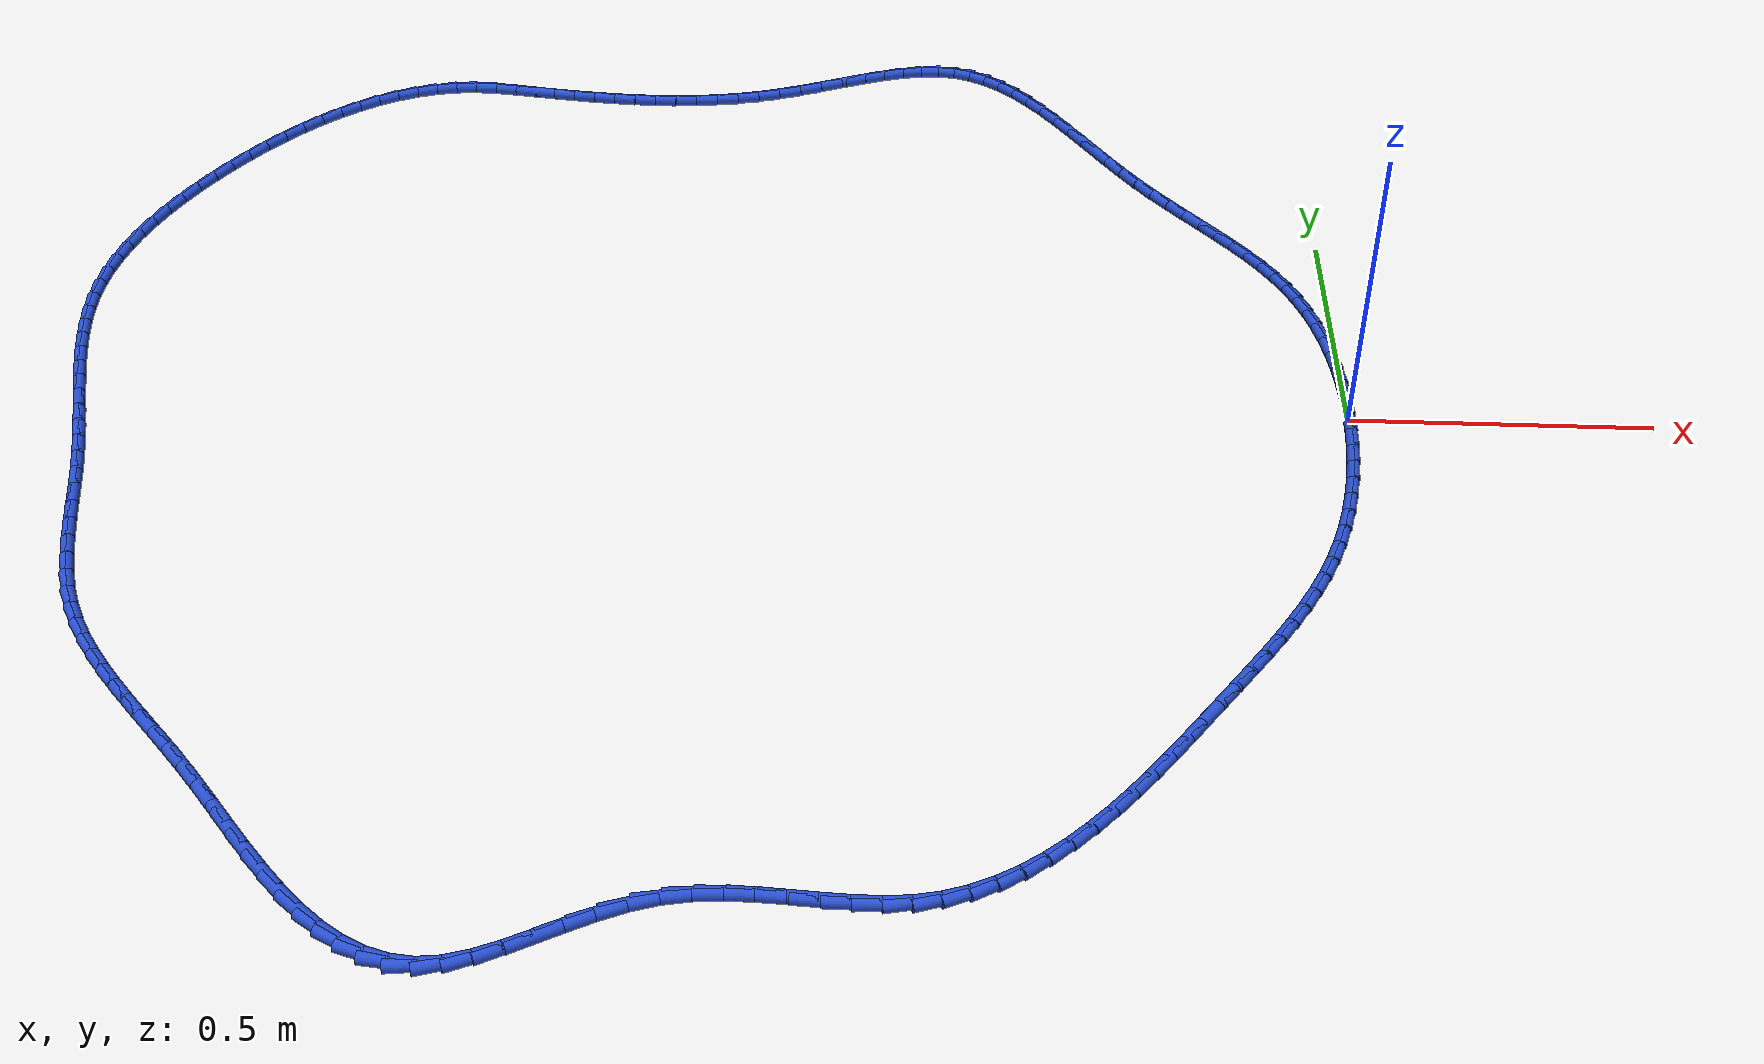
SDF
<sdf version="1.6">
 <world name="default">
  <light name="sun" type="directional">
   <pose>0 0 10 0 -0 0</pose>
   <diffuse>0.8 0.8 0.8 1</diffuse>
   <specular>0.2 0.2 0.2 1</specular>
   <attenuation>
    <range>1000</range>
    <constant>0.9</constant>
    <linear>0.01</linear>
    <quadratic>0.001</quadratic>
   </attenuation>
   <direction>-0.5 0.1 -0.9</direction>
  </light>
  <model name="ground_plane">
   <static>1</static>
   <link name="link">
    <collision name="collision">
     <geometry><plane><normal>0 0 1</normal><size>100 100</size></plane></geometry>
     <surface><friction><ode><mu>100</mu><mu2>50</mu2></ode></friction></surface>
    </collision>
    <visual name="visual">
     <cast_shadows>0</cast_shadows>
     <geometry><plane><normal>0 0 1</normal><size>100 100</size></plane></geometry>
     <material>
      <script><uri>file://media/materials/scripts/gazebo.material</uri><name>Gazebo/WhiteGlow</name></script>
     </material>
    </visual>
   </link>
  </model>
  <gravity>0 0 -9.8</gravity>
  <magnetic_field>6e-06 2.3e-05 -4.2e-05</magnetic_field>
  <atmosphere type="adiabatic"/>
  <physics name="default_physics" default="0" type="ode">
   <max_step_size>0.001</max_step_size>
   <real_time_factor>1</real_time_factor>
   <real_time_update_rate>1000</real_time_update_rate>
  </physics>
  <scene><ambient>0.4 0.4 0.4 1</ambient><background>0.7 0.7 0.7 1</background><shadows>1</shadows></scene>
  <spherical_coordinates>
   <surface_model>EARTH_WGS84</surface_model>
   <latitude_deg>0</latitude_deg>
   <longitude_deg>0</longitude_deg>
   <elevation>0</elevation>
   <heading_deg>0</heading_deg>
  </spherical_coordinates>
  <model name="line">
   <link name="link_0">
    <pose>2.6020852139652106e-18 -6.938893903907228e-17 0.01 0 1.57 -1.563608734815264</pose>
    <collision name="collision">
     <geometry><cylinder><radius>0.01</radius><length>0.08</length></cylinder></geometry>
    </collision>
    <visual name="visual">
     <material>
      <script><name>Gazebo/Blue</name><uri>file://media/materials/scripts/gazebo.material</uri></script>
     </material>
     <geometry><cylinder><radius>0.01</radius><length>0.08</length></cylinder></geometry>
    </visual>
   </link>
   <link name="link_1">
    <pose>-0.00030403188105106426 0.04229881806253479 0.01 0 1.57 -1.5273704567349236</pose>
    <collision name="collision">
     <geometry><cylinder><radius>0.01</radius><length>0.08</length></cylinder></geometry>
    </collision>
    <visual name="visual">
     <material>
      <script><name>Gazebo/Blue</name><uri>file://media/materials/scripts/gazebo.material</uri></script>
     </material>
     <geometry><cylinder><radius>0.01</radius><length>0.08</length></cylinder></geometry>
    </visual>
   </link>
   <link name="link_2">
    <pose>-0.002140272123697122 0.08455671250576582 0.01 0 1.57 -1.4880241802549388</pose>
    <collision name="collision">
     <geometry><cylinder><radius>0.01</radius><length>0.08</length></cylinder></geometry>
    </collision>
    <visual name="visual">
     <material>
      <script><name>Gazebo/Blue</name><uri>file://media/materials/scripts/gazebo.material</uri></script>
     </material>
     <geometry><cylinder><radius>0.01</radius><length>0.08</length></cylinder></geometry>
    </visual>
   </link>
   <link name="link_3">
    <pose>-0.005625227665629827 0.12656351440490687 0.01 0 1.57 -1.4450910302844981</pose>
    <collision name="collision">
     <geometry><cylinder><radius>0.01</radius><length>0.08</length></cylinder></geometry>
    </collision>
    <visual name="visual">
     <material>
      <script><name>Gazebo/Blue</name><uri>file://media/materials/scripts/gazebo.material</uri></script>
     </material>
     <geometry><cylinder><radius>0.01</radius><length>0.08</length></cylinder></geometry>
    </visual>
   </link>
   <link name="link_4">
    <pose>-0.010875405444540843 0.1681090548351718 0.01 0 1.57 -1.398050688930605</pose>
    <collision name="collision">
     <geometry><cylinder><radius>0.01</radius><length>0.08</length></cylinder></geometry>
    </collision>
    <visual name="visual">
     <material>
      <script><name>Gazebo/Blue</name><uri>file://media/materials/scripts/gazebo.material</uri></script>
     </material>
     <geometry><cylinder><radius>0.01</radius><length>0.08</length></cylinder></geometry>
    </visual>
   </link>
   <link name="link_5">
    <pose>-0.018007312398121825 0.20898316487177454 0.01 0 1.57 -1.3463466222002347</pose>
    <collision name="collision">
     <geometry><cylinder><radius>0.01</radius><length>0.08</length></cylinder></geometry>
    </collision>
    <visual name="visual">
     <material>
      <script><name>Gazebo/Blue</name><uri>file://media/materials/scripts/gazebo.material</uri></script>
     </material>
     <geometry><cylinder><radius>0.01</radius><length>0.08</length></cylinder></geometry>
    </visual>
   </link>
   <link name="link_6">
    <pose>-0.02713745546406443 0.24897567558992892 0.01 0 1.57 -1.289400566973975</pose>
    <collision name="collision">
     <geometry><cylinder><radius>0.01</radius><length>0.08</length></cylinder></geometry>
    </collision>
    <visual name="visual">
     <material>
      <script><name>Gazebo/Blue</name><uri>file://media/materials/scripts/gazebo.material</uri></script>
     </material>
     <geometry><cylinder><radius>0.01</radius><length>0.08</length></cylinder></geometry>
    </visual>
   </link>
   <link name="link_7">
    <pose>-0.03838234158006031 0.28787641806484876 0.01 0 1.57 -1.2266408279061143</pose>
    <collision name="collision">
     <geometry><cylinder><radius>0.01</radius><length>0.08</length></cylinder></geometry>
    </collision>
    <visual name="visual">
     <material>
      <script><name>Gazebo/Blue</name><uri>file://media/materials/scripts/gazebo.material</uri></script>
     </material>
     <geometry><cylinder><radius>0.01</radius><length>0.08</length></cylinder></geometry>
    </visual>
   </link>
   <link name="link_8">
    <pose>-0.051858477683801155 0.32547522337174817 0.01 0 1.57 -1.1575497465611457</pose>
    <collision name="collision">
     <geometry><cylinder><radius>0.01</radius><length>0.08</length></cylinder></geometry>
    </collision>
    <visual name="visual">
     <material>
      <script><name>Gazebo/Blue</name><uri>file://media/materials/scripts/gazebo.material</uri></script>
     </material>
     <geometry><cylinder><radius>0.01</radius><length>0.08</length></cylinder></geometry>
    </visual>
   </link>
   <link name="link_9">
    <pose>-0.06768237066134959 0.3615619226563367 0.01 0 1.57 -1.0845055881657066</pose>
    <collision name="collision">
     <geometry><cylinder><radius>0.01</radius><length>0.08</length></cylinder></geometry>
    </collision>
    <visual name="visual">
     <material>
      <script><name>Gazebo/Blue</name><uri>file://media/materials/scripts/gazebo.material</uri></script>
     </material>
     <geometry><cylinder><radius>0.01</radius><length>0.08</length></cylinder></geometry>
    </visual>
   </link>
   <link name="link_10">
    <pose>-0.08589967834813804 0.3960230866803879 0.01 0 1.57 -1.0188755373688974</pose>
    <collision name="collision">
     <geometry><cylinder><radius>0.01</radius><length>0.08</length></cylinder></geometry>
    </collision>
    <visual name="visual">
     <material>
      <script><name>Gazebo/Blue</name><uri>file://media/materials/scripts/gazebo.material</uri></script>
     </material>
     <geometry><cylinder><radius>0.01</radius><length>0.08</length></cylinder></geometry>
    </visual>
   </link>
   <link name="link_11">
    <pose>-0.1062802775958039 0.429121846600665 0.01 0 1.57 -0.9646249978101762</pose>
    <collision name="collision">
     <geometry><cylinder><radius>0.01</radius><length>0.08</length></cylinder></geometry>
    </collision>
    <visual name="visual">
     <material>
      <script><name>Gazebo/Blue</name><uri>file://media/materials/scripts/gazebo.material</uri></script>
     </material>
     <geometry><cylinder><radius>0.01</radius><length>0.08</length></cylinder></geometry>
    </visual>
   </link>
   <link name="link_12">
    <pose>-0.12852695292763466 0.46121294363825344 0.01 0 1.57 -0.9224898749275928</pose>
    <collision name="collision">
     <geometry><cylinder><radius>0.01</radius><length>0.08</length></cylinder></geometry>
    </collision>
    <visual name="visual">
     <material>
      <script><name>Gazebo/Blue</name><uri>file://media/materials/scripts/gazebo.material</uri></script>
     </material>
     <geometry><cylinder><radius>0.01</radius><length>0.08</length></cylinder></geometry>
    </visual>
   </link>
   <link name="link_13">
    <pose>-0.15234248886691762 0.49265111901423847 0.01 0 1.57 -0.8926344642741078</pose>
    <collision name="collision">
     <geometry><cylinder><radius>0.01</radius><length>0.08</length></cylinder></geometry>
    </collision>
    <visual name="visual">
     <material>
      <script><name>Gazebo/Blue</name><uri>file://media/materials/scripts/gazebo.material</uri></script>
     </material>
     <geometry><cylinder><radius>0.01</radius><length>0.08</length></cylinder></geometry>
    </visual>
   </link>
   <link name="link_14">
    <pose>-0.1774296699369401 0.5237911139497056 0.01 0 1.57 -0.8748394649555942</pose>
    <collision name="collision">
     <geometry><cylinder><radius>0.01</radius><length>0.08</length></cylinder></geometry>
    </collision>
    <visual name="visual">
     <material>
      <script><name>Gazebo/Blue</name><uri>file://media/materials/scripts/gazebo.material</uri></script>
     </material>
     <geometry><cylinder><radius>0.01</radius><length>0.08</length></cylinder></geometry>
    </visual>
   </link>
   <link name="link_15">
    <pose>-0.20349128066098954 0.5549876696657402 0.01 0 1.57 -0.8686552928595721</pose>
    <collision name="collision">
     <geometry><cylinder><radius>0.01</radius><length>0.08</length></cylinder></geometry>
    </collision>
    <visual name="visual">
     <material>
      <script><name>Gazebo/Blue</name><uri>file://media/materials/scripts/gazebo.material</uri></script>
     </material>
     <geometry><cylinder><radius>0.01</radius><length>0.08</length></cylinder></geometry>
    </visual>
   </link>
   <link name="link_16">
    <pose>-0.23023010556235338 0.5865955273834276 0.01 0 1.57 -0.8735009277398005</pose>
    <collision name="collision">
     <geometry><cylinder><radius>0.01</radius><length>0.08</length></cylinder></geometry>
    </collision>
    <visual name="visual">
     <material>
      <script><name>Gazebo/Blue</name><uri>file://media/materials/scripts/gazebo.material</uri></script>
     </material>
     <geometry><cylinder><radius>0.01</radius><length>0.08</length></cylinder></geometry>
    </visual>
   </link>
   <link name="link_17">
    <pose>-0.25734892916431884 0.6189694283238532 0.01 0 1.57 -0.8887104548957693</pose>
    <collision name="collision">
     <geometry><cylinder><radius>0.01</radius><length>0.08</length></cylinder></geometry>
    </collision>
    <visual name="visual">
     <material>
      <script><name>Gazebo/Blue</name><uri>file://media/materials/scripts/gazebo.material</uri></script>
     </material>
     <geometry><cylinder><radius>0.01</radius><length>0.08</length></cylinder></geometry>
    </visual>
   </link>
   <link name="link_18">
    <pose>-0.2845505359901733 0.6524641137081022 0.01 0 1.57 -0.9135393723879417</pose>
    <collision name="collision">
     <geometry><cylinder><radius>0.01</radius><length>0.08</length></cylinder></geometry>
    </collision>
    <visual name="visual">
     <material>
      <script><name>Gazebo/Blue</name><uri>file://media/materials/scripts/gazebo.material</uri></script>
     </material>
     <geometry><cylinder><radius>0.01</radius><length>0.08</length></cylinder></geometry>
    </visual>
   </link>
   <link name="link_19">
    <pose>-0.31153771056320423 0.6874343247572603 0.01 0 1.57 -0.9464577211058722</pose>
    <collision name="collision">
     <geometry><cylinder><radius>0.01</radius><length>0.08</length></cylinder></geometry>
    </collision>
    <visual name="visual">
     <material>
      <script><name>Gazebo/Blue</name><uri>file://media/materials/scripts/gazebo.material</uri></script>
     </material>
     <geometry><cylinder><radius>0.01</radius><length>0.08</length></cylinder></geometry>
    </visual>
   </link>
   <link name="link_20">
    <pose>-0.33802834882138205 0.7242024044399585 0.01 0 1.57 -0.9755999037970234</pose>
    <collision name="collision">
     <geometry><cylinder><radius>0.01</radius><length>0.08</length></cylinder></geometry>
    </collision>
    <visual name="visual">
     <material>
      <script><name>Gazebo/Blue</name><uri>file://media/materials/scripts/gazebo.material</uri></script>
     </material>
     <geometry><cylinder><radius>0.01</radius><length>0.08</length></cylinder></geometry>
    </visual>
   </link>
   <link name="link_21">
    <pose>-0.36399305997773446 0.7625488888420463 0.01 0 1.57 -0.9926076525637345</pose>
    <collision name="collision">
     <geometry><cylinder><radius>0.01</radius><length>0.08</length></cylinder></geometry>
    </collision>
    <visual name="visual">
     <material>
      <script><name>Gazebo/Blue</name><uri>file://media/materials/scripts/gazebo.material</uri></script>
     </material>
     <geometry><cylinder><radius>0.01</radius><length>0.08</length></cylinder></geometry>
    </visual>
   </link>
   <link name="link_22">
    <pose>-0.3896115639665261 0.8018059892512244 0.01 0 1.57 -0.9981308526406184</pose>
    <collision name="collision">
     <geometry><cylinder><radius>0.01</radius><length>0.08</length></cylinder></geometry>
    </collision>
    <visual name="visual">
     <material>
      <script><name>Gazebo/Blue</name><uri>file://media/materials/scripts/gazebo.material</uri></script>
     </material>
     <geometry><cylinder><radius>0.01</radius><length>0.08</length></cylinder></geometry>
    </visual>
   </link>
   <link name="link_23">
    <pose>-0.4150698734536968 0.8412924255969252 0.01 0 1.57 -0.9924119475564883</pose>
    <collision name="collision">
     <geometry><cylinder><radius>0.01</radius><length>0.08</length></cylinder></geometry>
    </collision>
    <visual name="visual">
     <material>
      <script><name>Gazebo/Blue</name><uri>file://media/materials/scripts/gazebo.material</uri></script>
     </material>
     <geometry><cylinder><radius>0.01</radius><length>0.08</length></cylinder></geometry>
    </visual>
   </link>
   <link name="link_24">
    <pose>-0.44055400110518583 0.8803269178085812 0.01 0 1.57 -0.9750084611272009</pose>
    <collision name="collision">
     <geometry><cylinder><radius>0.01</radius><length>0.08</length></cylinder></geometry>
    </collision>
    <visual name="visual">
     <material>
      <script><name>Gazebo/Blue</name><uri>file://media/materials/scripts/gazebo.material</uri></script>
     </material>
     <geometry><cylinder><radius>0.01</radius><length>0.08</length></cylinder></geometry>
    </visual>
   </link>
   <link name="link_25">
    <pose>-0.466249959586933 0.9182281858156249 0.01 0 1.57 -0.9447444199484701</pose>
    <collision name="collision">
     <geometry><cylinder><radius>0.01</radius><length>0.08</length></cylinder></geometry>
    </collision>
    <visual name="visual">
     <material>
      <script><name>Gazebo/Blue</name><uri>file://media/materials/scripts/gazebo.material</uri></script>
     </material>
     <geometry><cylinder><radius>0.01</radius><length>0.08</length></cylinder></geometry>
    </visual>
   </link>
   <link name="link_26">
    <pose>-0.49234376156487747 0.9543149495474886 0.01 0 1.57 -0.8996074238196139</pose>
    <collision name="collision">
     <geometry><cylinder><radius>0.01</radius><length>0.08</length></cylinder></geometry>
    </collision>
    <visual name="visual">
     <material>
      <script><name>Gazebo/Blue</name><uri>file://media/materials/scripts/gazebo.material</uri></script>
     </material>
     <geometry><cylinder><radius>0.01</radius><length>0.08</length></cylinder></geometry>
    </visual>
   </link>
   <link name="link_27">
    <pose>-0.5190214197049591 0.9879059289336051 0.01 0 1.57 -0.8366204130642738</pose>
    <collision name="collision">
     <geometry><cylinder><radius>0.01</radius><length>0.08</length></cylinder></geometry>
    </collision>
    <visual name="visual">
     <material>
      <script><name>Gazebo/Blue</name><uri>file://media/materials/scripts/gazebo.material</uri></script>
     </material>
     <geometry><cylinder><radius>0.01</radius><length>0.08</length></cylinder></geometry>
    </visual>
   </link>
   <link name="link_28">
    <pose>-0.5464689466731174 1.0183198439034067 0.01 0 1.57 -0.7517886933547984</pose>
    <collision name="collision">
     <geometry><cylinder><radius>0.01</radius><length>0.08</length></cylinder></geometry>
    </collision>
    <visual name="visual">
     <material>
      <script><name>Gazebo/Blue</name><uri>file://media/materials/scripts/gazebo.material</uri></script>
     </material>
     <geometry><cylinder><radius>0.01</radius><length>0.08</length></cylinder></geometry>
    </visual>
   </link>
   <link name="link_29">
    <pose>-0.5748723551352918 1.0448754143863261 0.01 0 1.57 -0.6403956141349085</pose>
    <collision name="collision">
     <geometry><cylinder><radius>0.01</radius><length>0.08</length></cylinder></geometry>
    </collision>
    <visual name="visual">
     <material>
      <script><name>Gazebo/Blue</name><uri>file://media/materials/scripts/gazebo.material</uri></script>
     </material>
     <geometry><cylinder><radius>0.01</radius><length>0.08</length></cylinder></geometry>
    </visual>
   </link>
   <link name="link_30">
    <pose>-0.6044176577574218 1.0668913603117955 0.01 0 1.57 -0.49822540100895485</pose>
    <collision name="collision">
     <geometry><cylinder><radius>0.01</radius><length>0.08</length></cylinder></geometry>
    </collision>
    <visual name="visual">
     <material>
      <script><name>Gazebo/Blue</name><uri>file://media/materials/scripts/gazebo.material</uri></script>
     </material>
     <geometry><cylinder><radius>0.01</radius><length>0.08</length></cylinder></geometry>
    </visual>
   </link>
   <link name="link_31">
    <pose>-0.6352908672054474 1.0836864016092478 0.01 0 1.57 -0.3244477196425939</pose>
    <collision name="collision">
     <geometry><cylinder><radius>0.01</radius><length>0.08</length></cylinder></geometry>
    </collision>
    <visual name="visual">
     <material>
      <script><name>Gazebo/Blue</name><uri>file://media/materials/scripts/gazebo.material</uri></script>
     </material>
     <geometry><cylinder><radius>0.01</radius><length>0.08</length></cylinder></geometry>
    </visual>
   </link>
   <link name="link_32">
    <pose>-0.6676779961453074 1.0945792582081149 0.01 0 1.57 -0.1265162315229476</pose>
    <collision name="collision">
     <geometry><cylinder><radius>0.01</radius><length>0.08</length></cylinder></geometry>
    </collision>
    <visual name="visual">
     <material>
      <script><name>Gazebo/Blue</name><uri>file://media/materials/scripts/gazebo.material</uri></script>
     </material>
     <geometry><cylinder><radius>0.01</radius><length>0.08</length></cylinder></geometry>
    </visual>
   </link>
   <link name="link_33">
    <pose>-0.701759262402985 1.098914245416494 0.01 0 1.57 0.05787647576022728</pose>
    <collision name="collision">
     <geometry><cylinder><radius>0.01</radius><length>0.08</length></cylinder></geometry>
    </collision>
    <visual name="visual">
     <material>
      <script><name>Gazebo/Blue</name><uri>file://media/materials/scripts/gazebo.material</uri></script>
     </material>
     <geometry><cylinder><radius>0.01</radius><length>0.08</length></cylinder></geometry>
    </visual>
   </link>
   <link name="link_34">
    <pose>-0.7375324432569059 1.096841504921368 0.01 0 1.57 0.19563576379664416</pose>
    <collision name="collision">
     <geometry><cylinder><radius>0.01</radius><length>0.08</length></cylinder></geometry>
    </collision>
    <visual name="visual">
     <material>
      <script><name>Gazebo/Blue</name><uri>file://media/materials/scripts/gazebo.material</uri></script>
     </material>
     <geometry><cylinder><radius>0.01</radius><length>0.08</length></cylinder></geometry>
    </visual>
   </link>
   <link name="link_35">
    <pose>-0.7747804914899324 1.0894600422871439 0.01 0 1.57 0.2911868342537742</pose>
    <collision name="collision">
     <geometry><cylinder><radius>0.01</radius><length>0.08</length></cylinder></geometry>
    </collision>
    <visual name="visual">
     <material>
      <script><name>Gazebo/Blue</name><uri>file://media/materials/scripts/gazebo.material</uri></script>
     </material>
     <geometry><cylinder><radius>0.01</radius><length>0.08</length></cylinder></geometry>
    </visual>
   </link>
   <link name="link_36">
    <pose>-0.8132740340001904 1.0779233055977104 0.01 0 1.57 0.35259745705870177</pose>
    <collision name="collision">
     <geometry><cylinder><radius>0.01</radius><length>0.08</length></cylinder></geometry>
    </collision>
    <visual name="visual">
     <material>
      <script><name>Gazebo/Blue</name><uri>file://media/materials/scripts/gazebo.material</uri></script>
     </material>
     <geometry><cylinder><radius>0.01</radius><length>0.08</length></cylinder></geometry>
    </visual>
   </link>
   <link name="link_37">
    <pose>-0.8527836976858049 1.0633847429369563 0.01 0 1.57 0.3862345757084237</pose>
    <collision name="collision">
     <geometry><cylinder><radius>0.01</radius><length>0.08</length></cylinder></geometry>
    </collision>
    <visual name="visual">
     <material>
      <script><name>Gazebo/Blue</name><uri>file://media/materials/scripts/gazebo.material</uri></script>
     </material>
     <geometry><cylinder><radius>0.01</radius><length>0.08</length></cylinder></geometry>
    </visual>
   </link>
   <link name="link_38">
    <pose>-0.8930801094449011 1.0469978023887707 0.01 0 1.57 0.3960305955299181</pose>
    <collision name="collision">
     <geometry><cylinder><radius>0.01</radius><length>0.08</length></cylinder></geometry>
    </collision>
    <visual name="visual">
     <material>
      <script><name>Gazebo/Blue</name><uri>file://media/materials/scripts/gazebo.material</uri></script>
     </material>
     <geometry><cylinder><radius>0.01</radius><length>0.08</length></cylinder></geometry>
    </visual>
   </link>
   <link name="link_39">
    <pose>-0.9339338961756044 1.029915932037041 0.01 0 1.57 0.3836557096702099</pose>
    <collision name="collision">
     <geometry><cylinder><radius>0.01</radius><length>0.08</length></cylinder></geometry>
    </collision>
    <visual name="visual">
     <material>
      <script><name>Gazebo/Blue</name><uri>file://media/materials/scripts/gazebo.material</uri></script>
     </material>
     <geometry><cylinder><radius>0.01</radius><length>0.08</length></cylinder></geometry>
    </visual>
   </link>
   <link name="link_40">
    <pose>-0.9751156847760408 1.0132925799656574 0.01 0 1.57 0.34877795378042464</pose>
    <collision name="collision">
     <geometry><cylinder><radius>0.01</radius><length>0.08</length></cylinder></geometry>
    </collision>
    <visual name="visual">
     <material>
      <script><name>Gazebo/Blue</name><uri>file://media/materials/scripts/gazebo.material</uri></script>
     </material>
     <geometry><cylinder><radius>0.01</radius><length>0.08</length></cylinder></geometry>
    </visual>
   </link>
   <link name="link_41">
    <pose>-1.0163961021443346 0.9982811942585081 0.01 0 1.57 0.2921159821964271</pose>
    <collision name="collision">
     <geometry><cylinder><radius>0.01</radius><length>0.08</length></cylinder></geometry>
    </collision>
    <visual name="visual">
     <material>
      <script><name>Gazebo/Blue</name><uri>file://media/materials/scripts/gazebo.material</uri></script>
     </material>
     <geometry><cylinder><radius>0.01</radius><length>0.08</length></cylinder></geometry>
    </visual>
   </link>
   <link name="link_42">
    <pose>-1.0575710310322233 0.9858991249480141 0.01 0 1.57 0.23035135408467605</pose>
    <collision name="collision">
     <geometry><cylinder><radius>0.01</radius><length>0.08</length></cylinder></geometry>
    </collision>
    <visual name="visual">
     <material>
      <script><name>Gazebo/Blue</name><uri>file://media/materials/scripts/gazebo.material</uri></script>
     </material>
     <geometry><cylinder><radius>0.01</radius><length>0.08</length></cylinder></geometry>
    </visual>
   </link>
   <link name="link_43">
    <pose>-1.098600895391843 0.976277046957294 0.01 0 1.57 0.17151627818310108</pose>
    <collision name="collision">
     <geometry><cylinder><radius>0.01</radius><length>0.08</length></cylinder></geometry>
    </collision>
    <visual name="visual">
     <material>
      <script><name>Gazebo/Blue</name><uri>file://media/materials/scripts/gazebo.material</uri></script>
     </material>
     <geometry><cylinder><radius>0.01</radius><length>0.08</length></cylinder></geometry>
    </visual>
   </link>
   <link name="link_44">
    <pose>-1.1395120227830668 0.9691904956550657 0.01 0 1.57 0.11648555332294579</pose>
    <collision name="collision">
     <geometry><cylinder><radius>0.01</radius><length>0.08</length></cylinder></geometry>
    </collision>
    <visual name="visual">
     <material>
      <script><name>Gazebo/Blue</name><uri>file://media/materials/scripts/gazebo.material</uri></script>
     </material>
     <geometry><cylinder><radius>0.01</radius><length>0.08</length></cylinder></geometry>
    </visual>
   </link>
   <link name="link_45">
    <pose>-1.1803309161928683 0.9644140610732937 0.01 0 1.57 0.06595374751297108</pose>
    <collision name="collision">
     <geometry><cylinder><radius>0.01</radius><length>0.08</length></cylinder></geometry>
    </collision>
    <visual name="visual">
     <material>
      <script><name>Gazebo/Blue</name><uri>file://media/materials/scripts/gazebo.material</uri></script>
     </material>
     <geometry><cylinder><radius>0.01</radius><length>0.08</length></cylinder></geometry>
    </visual>
   </link>
   <link name="link_46">
    <pose>-1.2210840786082213 0.9617223332439425 0.01 0 1.57 0.02044300290930315</pose>
    <collision name="collision">
     <geometry><cylinder><radius>0.01</radius><length>0.08</length></cylinder></geometry>
    </collision>
    <visual name="visual">
     <material>
      <script><name>Gazebo/Blue</name><uri>file://media/materials/scripts/gazebo.material</uri></script>
     </material>
     <geometry><cylinder><radius>0.01</radius><length>0.08</length></cylinder></geometry>
    </visual>
   </link>
   <link name="link_47">
    <pose>-1.2617980130160984 0.9608899021989759 0.01 0 1.57 -0.019688658423729716</pose>
    <collision name="collision">
     <geometry><cylinder><radius>0.01</radius><length>0.08</length></cylinder></geometry>
    </collision>
    <visual name="visual">
     <material>
      <script><name>Gazebo/Blue</name><uri>file://media/materials/scripts/gazebo.material</uri></script>
     </material>
     <geometry><cylinder><radius>0.01</radius><length>0.08</length></cylinder></geometry>
    </visual>
   </link>
   <link name="link_48">
    <pose>-1.3024992224034735 0.9616913579703584 0.01 0 1.57 -0.05422490227888521</pose>
    <collision name="collision">
     <geometry><cylinder><radius>0.01</radius><length>0.08</length></cylinder></geometry>
    </collision>
    <visual name="visual">
     <material>
      <script><name>Gazebo/Blue</name><uri>file://media/materials/scripts/gazebo.material</uri></script>
     </material>
     <geometry><cylinder><radius>0.01</radius><length>0.08</length></cylinder></geometry>
    </visual>
   </link>
   <link name="link_49">
    <pose>-1.3432142097573203 0.9639012905900541 0.01 0 1.57 -0.08306148001203718</pose>
    <collision name="collision">
     <geometry><cylinder><radius>0.01</radius><length>0.08</length></cylinder></geometry>
    </collision>
    <visual name="visual">
     <material>
      <script><name>Gazebo/Blue</name><uri>file://media/materials/scripts/gazebo.material</uri></script>
     </material>
     <geometry><cylinder><radius>0.01</radius><length>0.08</length></cylinder></geometry>
    </visual>
   </link>
   <link name="link_50">
    <pose>-1.3839694780646128 0.9672942900900277 0.01 0 1.57 -0.10617534546177798</pose>
    <collision name="collision">
     <geometry><cylinder><radius>0.01</radius><length>0.08</length></cylinder></geometry>
    </collision>
    <visual name="visual">
     <material>
      <script><name>Gazebo/Blue</name><uri>file://media/materials/scripts/gazebo.material</uri></script>
     </material>
     <geometry><cylinder><radius>0.01</radius><length>0.08</length></cylinder></geometry>
    </visual>
   </link>
   <link name="link_51">
    <pose>-1.4247915303123226 0.9716449465022425 0.01 0 1.57 -0.12359654684707527</pose>
    <collision name="collision">
     <geometry><cylinder><radius>0.01</radius><length>0.08</length></cylinder></geometry>
    </collision>
    <visual name="visual">
     <material>
      <script><name>Gazebo/Blue</name><uri>file://media/materials/scripts/gazebo.material</uri></script>
     </material>
     <geometry><cylinder><radius>0.01</radius><length>0.08</length></cylinder></geometry>
    </visual>
   </link>
   <link name="link_52">
    <pose>-1.4657068694874251 0.9767278498586636 0.01 0 1.57 -0.13538514307323052</pose>
    <collision name="collision">
     <geometry><cylinder><radius>0.01</radius><length>0.08</length></cylinder></geometry>
    </collision>
    <visual name="visual">
     <material>
      <script><name>Gazebo/Blue</name><uri>file://media/materials/scripts/gazebo.material</uri></script>
     </material>
     <geometry><cylinder><radius>0.01</radius><length>0.08</length></cylinder></geometry>
    </visual>
   </link>
   <link name="link_53">
    <pose>-1.5067419985768933 0.9823175901912551 0.01 0 1.57 -0.138193303921964</pose>
    <collision name="collision">
     <geometry><cylinder><radius>0.01</radius><length>0.08</length></cylinder></geometry>
    </collision>
    <visual name="visual">
     <material>
      <script><name>Gazebo/Blue</name><uri>file://media/materials/scripts/gazebo.material</uri></script>
     </material>
     <geometry><cylinder><radius>0.01</radius><length>0.08</length></cylinder></geometry>
    </visual>
   </link>
   <link name="link_54">
    <pose>-1.547884972023137 0.9880397461656728 0.01 0 1.57 -0.1101018982708035</pose>
    <collision name="collision">
     <geometry><cylinder><radius>0.01</radius><length>0.08</length></cylinder></geometry>
    </collision>
    <visual name="visual">
     <material>
      <script><name>Gazebo/Blue</name><uri>file://media/materials/scripts/gazebo.material</uri></script>
     </material>
     <geometry><cylinder><radius>0.01</radius><length>0.08</length></cylinder></geometry>
    </visual>
   </link>
   <link name="link_55">
    <pose>-1.5888791638228288 0.9925716117220321 0.01 0 1.57 -0.04065413062825103</pose>
    <collision name="collision">
     <geometry><cylinder><radius>0.01</radius><length>0.08</length></cylinder></geometry>
    </collision>
    <visual name="visual">
     <material>
      <script><name>Gazebo/Blue</name><uri>file://media/materials/scripts/gazebo.material</uri></script>
     </material>
     <geometry><cylinder><radius>0.01</radius><length>0.08</length></cylinder></geometry>
    </visual>
   </link>
   <link name="link_56">
    <pose>-1.6293720250139212 0.9942187213151098 0.01 0 1.57 0.0720433524379047</pose>
    <collision name="collision">
     <geometry><cylinder><radius>0.01</radius><length>0.08</length></cylinder></geometry>
    </collision>
    <visual name="visual">
     <material>
      <script><name>Gazebo/Blue</name><uri>file://media/materials/scripts/gazebo.material</uri></script>
     </material>
     <geometry><cylinder><radius>0.01</radius><length>0.08</length></cylinder></geometry>
    </visual>
   </link>
   <link name="link_57">
    <pose>-1.669021014763774 0.9913573230065676 0.01 0 1.57 0.20135852837922488</pose>
    <collision name="collision">
     <geometry><cylinder><radius>0.01</radius><length>0.08</length></cylinder></geometry>
    </collision>
    <visual name="visual">
     <material>
      <script><name>Gazebo/Blue</name><uri>file://media/materials/scripts/gazebo.material</uri></script>
     </material>
     <geometry><cylinder><radius>0.01</radius><length>0.08</length></cylinder></geometry>
    </visual>
   </link>
   <link name="link_58">
    <pose>-1.707642281819672 0.9834737654374085 0.01 0 1.57 0.32253798854013965</pose>
    <collision name="collision">
     <geometry><cylinder><radius>0.01</radius><length>0.08</length></cylinder></geometry>
    </collision>
    <visual name="visual">
     <material>
      <script><name>Gazebo/Blue</name><uri>file://media/materials/scripts/gazebo.material</uri></script>
     </material>
     <geometry><cylinder><radius>0.01</radius><length>0.08</length></cylinder></geometry>
    </visual>
   </link>
   <link name="link_59">
    <pose>-1.7451770468738184 0.9709293282842901 0.01 0 1.57 0.43294248800243706</pose>
    <collision name="collision">
     <geometry><cylinder><radius>0.01</radius><length>0.08</length></cylinder></geometry>
    </collision>
    <visual name="visual">
     <material>
      <script><name>Gazebo/Blue</name><uri>file://media/materials/scripts/gazebo.material</uri></script>
     </material>
     <geometry><cylinder><radius>0.01</radius><length>0.08</length></cylinder></geometry>
    </visual>
   </link>
   <link name="link_60">
    <pose>-1.7815699207261406 0.9541090064580302 0.01 0 1.57 0.5318912590642909</pose>
    <collision name="collision">
     <geometry><cylinder><radius>0.01</radius><length>0.08</length></cylinder></geometry>
    </collision>
    <visual name="visual">
     <material>
      <script><name>Gazebo/Blue</name><uri>file://media/materials/scripts/gazebo.material</uri></script>
     </material>
     <geometry><cylinder><radius>0.01</radius><length>0.08</length></cylinder></geometry>
    </visual>
   </link>
   <link name="link_61">
    <pose>-1.8167655141765653 0.9333977948694459 0.01 0 1.57 0.6197061858737413</pose>
    <collision name="collision">
     <geometry><cylinder><radius>0.01</radius><length>0.08</length></cylinder></geometry>
    </collision>
    <visual name="visual">
     <material>
      <script><name>Gazebo/Blue</name><uri>file://media/materials/scripts/gazebo.material</uri></script>
     </material>
     <geometry><cylinder><radius>0.01</radius><length>0.08</length></cylinder></geometry>
    </visual>
   </link>
   <link name="link_62">
    <pose>-1.8507084380250185 0.9091806884293553 0.01 0 1.57 0.6973058346139636</pose>
    <collision name="collision">
     <geometry><cylinder><radius>0.01</radius><length>0.08</length></cylinder></geometry>
    </collision>
    <visual name="visual">
     <material>
      <script><name>Gazebo/Blue</name><uri>file://media/materials/scripts/gazebo.material</uri></script>
     </material>
     <geometry><cylinder><radius>0.01</radius><length>0.08</length></cylinder></geometry>
    </visual>
   </link>
   <link name="link_63">
    <pose>-1.8833433030714264 0.8818426820485752 0.01 0 1.57 0.7658799116931142</pose>
    <collision name="collision">
     <geometry><cylinder><radius>0.01</radius><length>0.08</length></cylinder></geometry>
    </collision>
    <visual name="visual">
     <material>
      <script><name>Gazebo/Blue</name><uri>file://media/materials/scripts/gazebo.material</uri></script>
     </material>
     <geometry><cylinder><radius>0.01</radius><length>0.08</length></cylinder></geometry>
    </visual>
   </link>
   <link name="link_64">
    <pose>-1.914614720115715 0.8517687706379241 0.01 0 1.57 0.8266776714309082</pose>
    <collision name="collision">
     <geometry><cylinder><radius>0.01</radius><length>0.08</length></cylinder></geometry>
    </collision>
    <visual name="visual">
     <material>
      <script><name>Gazebo/Blue</name><uri>file://media/materials/scripts/gazebo.material</uri></script>
     </material>
     <geometry><cylinder><radius>0.01</radius><length>0.08</length></cylinder></geometry>
    </visual>
   </link>
   <link name="link_65">
    <pose>-1.9444672999578119 0.8193439491082191 0.01 0 1.57 0.8808925565863249</pose>
    <collision name="collision">
     <geometry><cylinder><radius>0.01</radius><length>0.08</length></cylinder></geometry>
    </collision>
    <visual name="visual">
     <material>
      <script><name>Gazebo/Blue</name><uri>file://media/materials/scripts/gazebo.material</uri></script>
     </material>
     <geometry><cylinder><radius>0.01</radius><length>0.08</length></cylinder></geometry>
    </visual>
   </link>
   <link name="link_66">
    <pose>-1.9728456533976435 0.7849532123702778 0.01 0 1.57 0.929612253341343</pose>
    <collision name="collision">
     <geometry><cylinder><radius>0.01</radius><length>0.08</length></cylinder></geometry>
    </collision>
    <visual name="visual">
     <material>
      <script><name>Gazebo/Blue</name><uri>file://media/materials/scripts/gazebo.material</uri></script>
     </material>
     <geometry><cylinder><radius>0.01</radius><length>0.08</length></cylinder></geometry>
    </visual>
   </link>
   <link name="link_67">
    <pose>-1.9996943912351357 0.7489815553349181 0.01 0 1.57 0.9738077752511692</pose>
    <collision name="collision">
     <geometry><cylinder><radius>0.01</radius><length>0.08</length></cylinder></geometry>
    </collision>
    <visual name="visual">
     <material>
      <script><name>Gazebo/Blue</name><uri>file://media/materials/scripts/gazebo.material</uri></script>
     </material>
     <geometry><cylinder><radius>0.01</radius><length>0.08</length></cylinder></geometry>
    </visual>
   </link>
   <link name="link_68">
    <pose>-2.024958124270215 0.7118139729129569 0.01 0 1.57 1.0143438582423232</pose>
    <collision name="collision">
     <geometry><cylinder><radius>0.01</radius><length>0.08</length></cylinder></geometry>
    </collision>
    <visual name="visual">
     <material>
      <script><name>Gazebo/Blue</name><uri>file://media/materials/scripts/gazebo.material</uri></script>
     </material>
     <geometry><cylinder><radius>0.01</radius><length>0.08</length></cylinder></geometry>
    </visual>
   </link>
   <link name="link_69">
    <pose>-2.0485814633028077 0.6738354600152128 0.01 0 1.57 1.0521744910434263</pose>
    <collision name="collision">
     <geometry><cylinder><radius>0.01</radius><length>0.08</length></cylinder></geometry>
    </collision>
    <visual name="visual">
     <material>
      <script><name>Gazebo/Blue</name><uri>file://media/materials/scripts/gazebo.material</uri></script>
     </material>
     <geometry><cylinder><radius>0.01</radius><length>0.08</length></cylinder></geometry>
    </visual>
   </link>
   <link name="link_70">
    <pose>-2.0705071193459297 0.6354188200036454 0.01 0 1.57 1.0906015369011544</pose>
    <collision name="collision">
     <geometry><cylinder><radius>0.01</radius><length>0.08</length></cylinder></geometry>
    </collision>
    <visual name="visual">
     <material>
      <script><name>Gazebo/Blue</name><uri>file://media/materials/scripts/gazebo.material</uri></script>
     </material>
     <geometry><cylinder><radius>0.01</radius><length>0.08</length></cylinder></geometry>
    </visual>
   </link>
   <link name="link_71">
    <pose>-2.09064855127912 0.5967491358108904 0.01 0 1.57 1.1320293997683217</pose>
    <collision name="collision">
     <geometry><cylinder><radius>0.01</radius><length>0.08</length></cylinder></geometry>
    </collision>
    <visual name="visual">
     <material>
      <script><name>Gazebo/Blue</name><uri>file://media/materials/scripts/gazebo.material</uri></script>
     </material>
     <geometry><cylinder><radius>0.01</radius><length>0.08</length></cylinder></geometry>
    </visual>
   </link>
   <link name="link_72">
    <pose>-2.1088962697177145 0.5578642239142902 0.01 0 1.57 1.1767407733456</pose>
    <collision name="collision">
     <geometry><cylinder><radius>0.01</radius><length>0.08</length></cylinder></geometry>
    </collision>
    <visual name="visual">
     <material>
      <script><name>Gazebo/Blue</name><uri>file://media/materials/scripts/gazebo.material</uri></script>
     </material>
     <geometry><cylinder><radius>0.01</radius><length>0.08</length></cylinder></geometry>
    </visual>
   </link>
   <link name="link_73">
    <pose>-2.125140169591737 0.5187979497387637 0.01 0 1.57 1.2249468748099253</pose>
    <collision name="collision">
     <geometry><cylinder><radius>0.01</radius><length>0.08</length></cylinder></geometry>
    </collision>
    <visual name="visual">
     <material>
      <script><name>Gazebo/Blue</name><uri>file://media/materials/scripts/gazebo.material</uri></script>
     </material>
     <geometry><cylinder><radius>0.01</radius><length>0.08</length></cylinder></geometry>
    </visual>
   </link>
   <link name="link_74">
    <pose>-2.1392701458312042 0.4795841787092292 0.01 0 1.57 1.2768283758326175</pose>
    <collision name="collision">
     <geometry><cylinder><radius>0.01</radius><length>0.08</length></cylinder></geometry>
    </collision>
    <visual name="visual">
     <material>
      <script><name>Gazebo/Blue</name><uri>file://media/materials/scripts/gazebo.material</uri></script>
     </material>
     <geometry><cylinder><radius>0.01</radius><length>0.08</length></cylinder></geometry>
    </visual>
   </link>
   <link name="link_75">
    <pose>-2.1511760933661352 0.44025677625060633 0.01 0 1.57 1.332515590748334</pose>
    <collision name="collision">
     <geometry><cylinder><radius>0.01</radius><length>0.08</length></cylinder></geometry>
    </collision>
    <visual name="visual">
     <material>
      <script><name>Gazebo/Blue</name><uri>file://media/materials/scripts/gazebo.material</uri></script>
     </material>
     <geometry><cylinder><radius>0.01</radius><length>0.08</length></cylinder></geometry>
    </visual>
   </link>
   <link name="link_76">
    <pose>-2.16074790712655 0.4008496077878136 0.01 0 1.57 1.3920645810216832</pose>
    <collision name="collision">
     <geometry><cylinder><radius>0.01</radius><length>0.08</length></cylinder></geometry>
    </collision>
    <visual name="visual">
     <material>
      <script><name>Gazebo/Blue</name><uri>file://media/materials/scripts/gazebo.material</uri></script>
     </material>
     <geometry><cylinder><radius>0.01</radius><length>0.08</length></cylinder></geometry>
    </visual>
   </link>
   <link name="link_77">
    <pose>-2.1678754820424677 0.3613965387457695 0.01 0 1.57 1.455430504855217</pose>
    <collision name="collision">
     <geometry><cylinder><radius>0.01</radius><length>0.08</length></cylinder></geometry>
    </collision>
    <visual name="visual">
     <material>
      <script><name>Gazebo/Blue</name><uri>file://media/materials/scripts/gazebo.material</uri></script>
     </material>
     <geometry><cylinder><radius>0.01</radius><length>0.08</length></cylinder></geometry>
    </visual>
   </link>
   <link name="link_78">
    <pose>-2.1724487130439067 0.3219314345493935 0.01 0 1.57 1.5224409580854117</pose>
    <collision name="collision">
     <geometry><cylinder><radius>0.01</radius><length>0.08</length></cylinder></geometry>
    </collision>
    <visual name="visual">
     <material>
      <script><name>Gazebo/Blue</name><uri>file://media/materials/scripts/gazebo.material</uri></script>
     </material>
     <geometry><cylinder><radius>0.01</radius><length>0.08</length></cylinder></geometry>
    </visual>
   </link>
   <link name="link_79">
    <pose>-2.174357495060886 0.28248816062360377 0.01 0 1.57 -1.5491895214473776</pose>
    <collision name="collision">
     <geometry><cylinder><radius>0.01</radius><length>0.08</length></cylinder></geometry>
    </collision>
    <visual name="visual">
     <material>
      <script><name>Gazebo/Blue</name><uri>file://media/materials/scripts/gazebo.material</uri></script>
     </material>
     <geometry><cylinder><radius>0.01</radius><length>0.08</length></cylinder></geometry>
    </visual>
   </link>
   <link name="link_80">
    <pose>-2.1735062755265266 0.2430983919162099 0.01 0 1.57 -1.482722858988238</pose>
    <collision name="collision">
     <geometry><cylinder><radius>0.01</radius><length>0.08</length></cylinder></geometry>
    </collision>
    <visual name="visual">
     <material>
      <script><name>Gazebo/Blue</name><uri>file://media/materials/scripts/gazebo.material</uri></script>
     </material>
     <geometry><cylinder><radius>0.01</radius><length>0.08</length></cylinder></geometry>
    </visual>
   </link>
   <link name="link_81">
    <pose>-2.170032508559958 0.203758730658761 0.01 0 1.57 -1.4250622208657993</pose>
    <collision name="collision">
     <geometry><cylinder><radius>0.01</radius><length>0.08</length></cylinder></geometry>
    </collision>
    <visual name="visual">
     <material>
      <script><name>Gazebo/Blue</name><uri>file://media/materials/scripts/gazebo.material</uri></script>
     </material>
     <geometry><cylinder><radius>0.01</radius><length>0.08</length></cylinder></geometry>
    </visual>
   </link>
   <link name="link_82">
    <pose>-2.1642611560540788 0.16443755497019016 0.01 0 1.57 -1.3765405630836445</pose>
    <collision name="collision">
     <geometry><cylinder><radius>0.01</radius><length>0.08</length></cylinder></geometry>
    </collision>
    <visual name="visual">
     <material>
      <script><name>Gazebo/Blue</name><uri>file://media/materials/scripts/gazebo.material</uri></script>
     </material>
     <geometry><cylinder><radius>0.01</radius><length>0.08</length></cylinder></geometry>
    </visual>
   </link>
   <link name="link_83">
    <pose>-2.1565224977799216 0.12510244250986563 0.01 0 1.57 -1.3370737299560842</pose>
    <collision name="collision">
     <geometry><cylinder><radius>0.01</radius><length>0.08</length></cylinder></geometry>
    </collision>
    <visual name="visual">
     <material>
      <script><name>Gazebo/Blue</name><uri>file://media/materials/scripts/gazebo.material</uri></script>
     </material>
     <geometry><cylinder><radius>0.01</radius><length>0.08</length></cylinder></geometry>
    </visual>
   </link>
   <link name="link_84">
    <pose>-2.147146813508521 0.08572097093715417 0.01 0 1.57 -1.3064194196465648</pose>
    <collision name="collision">
     <geometry><cylinder><radius>0.01</radius><length>0.08</length></cylinder></geometry>
    </collision>
    <visual name="visual">
     <material>
      <script><name>Gazebo/Blue</name><uri>file://media/materials/scripts/gazebo.material</uri></script>
     </material>
     <geometry><cylinder><radius>0.01</radius><length>0.08</length></cylinder></geometry>
    </visual>
   </link>
   <link name="link_85">
    <pose>-2.136464383010908 0.04626071791142376 0.01 0 1.57 -1.2842743519416115</pose>
    <collision name="collision">
     <geometry><cylinder><radius>0.01</radius><length>0.08</length></cylinder></geometry>
    </collision>
    <visual name="visual">
     <material>
      <script><name>Gazebo/Blue</name><uri>file://media/materials/scripts/gazebo.material</uri></script>
     </material>
     <geometry><cylinder><radius>0.01</radius><length>0.08</length></cylinder></geometry>
    </visual>
   </link>
   <link name="link_86">
    <pose>-2.124805486058117 0.00668926109204163 0.01 0 1.57 -1.2703420955373987</pose>
    <collision name="collision">
     <geometry><cylinder><radius>0.01</radius><length>0.08</length></cylinder></geometry>
    </collision>
    <visual name="visual">
     <material>
      <script><name>Gazebo/Blue</name><uri>file://media/materials/scripts/gazebo.material</uri></script>
     </material>
     <geometry><cylinder><radius>0.01</radius><length>0.08</length></cylinder></geometry>
    </visual>
   </link>
   <link name="link_87">
    <pose>-2.112500402421179 -0.03302582186162491 0.01 0 1.57 -1.2643752280755183</pose>
    <collision name="collision">
     <geometry><cylinder><radius>0.01</radius><length>0.08</length></cylinder></geometry>
    </collision>
    <visual name="visual">
     <material>
      <script><name>Gazebo/Blue</name><uri>file://media/materials/scripts/gazebo.material</uri></script>
     </material>
     <geometry><cylinder><radius>0.01</radius><length>0.08</length></cylinder></geometry>
    </visual>
   </link>
   <link name="link_88">
    <pose>-2.099879411871128 -0.07291695329020839 0.01 0 1.57 -1.2661972590735602</pose>
    <collision name="collision">
     <geometry><cylinder><radius>0.01</radius><length>0.08</length></cylinder></geometry>
    </collision>
    <visual name="visual">
     <material>
      <script><name>Gazebo/Blue</name><uri>file://media/materials/scripts/gazebo.material</uri></script>
     </material>
     <geometry><cylinder><radius>0.01</radius><length>0.08</length></cylinder></geometry>
    </visual>
   </link>
   <link name="link_89">
    <pose>-2.087272794178996 -0.11301655553434213 0.01 0 1.57 -1.2757089311542888</pose>
    <collision name="collision">
     <geometry><cylinder><radius>0.01</radius><length>0.08</length></cylinder></geometry>
    </collision>
    <visual name="visual">
     <material>
      <script><name>Gazebo/Blue</name><uri>file://media/materials/scripts/gazebo.material</uri></script>
     </material>
     <geometry><cylinder><radius>0.01</radius><length>0.08</length></cylinder></geometry>
    </visual>
   </link>
   <link name="link_90">
    <pose>-2.075010829115816 -0.15335705093465724 0.01 0 1.57 -1.292881722788589</pose>
    <collision name="collision">
     <geometry><cylinder><radius>0.01</radius><length>0.08</length></cylinder></geometry>
    </collision>
    <visual name="visual">
     <material>
      <script><name>Gazebo/Blue</name><uri>file://media/materials/scripts/gazebo.material</uri></script>
     </material>
     <geometry><cylinder><radius>0.01</radius><length>0.08</length></cylinder></geometry>
    </visual>
   </link>
   <link name="link_91">
    <pose>-2.0634237964526205 -0.19397086183178702 0.01 0 1.57 -1.3160131389282108</pose>
    <collision name="collision">
     <geometry><cylinder><radius>0.01</radius><length>0.08</length></cylinder></geometry>
    </collision>
    <visual name="visual">
     <material>
      <script><name>Gazebo/Blue</name><uri>file://media/materials/scripts/gazebo.material</uri></script>
     </material>
     <geometry><cylinder><radius>0.01</radius><length>0.08</length></cylinder></geometry>
    </visual>
   </link>
   <link name="link_92">
    <pose>-2.0527730795088215 -0.23486544196000003 0.01 0 1.57 -1.3333577851280374</pose>
    <collision name="collision">
     <geometry><cylinder><radius>0.01</radius><length>0.08</length></cylinder></geometry>
    </collision>
    <visual name="visual">
     <material>
      <script><name>Gazebo/Blue</name><uri>file://media/materials/scripts/gazebo.material</uri></script>
     </material>
     <geometry><cylinder><radius>0.01</radius><length>0.08</length></cylinder></geometry>
    </visual>
   </link>
   <link name="link_93">
    <pose>-2.0428480891049157 -0.2758771985734834 0.01 0 1.57 -1.3400387982809687</pose>
    <collision name="collision">
     <geometry><cylinder><radius>0.01</radius><length>0.08</length></cylinder></geometry>
    </collision>
    <visual name="visual">
     <material>
      <script><name>Gazebo/Blue</name><uri>file://media/materials/scripts/gazebo.material</uri></script>
     </material>
     <geometry><cylinder><radius>0.01</radius><length>0.08</length></cylinder></geometry>
    </visual>
   </link>
   <link name="link_94">
    <pose>-2.0332404293103887 -0.31677085223159634 0.01 0 1.57 -1.3359560117071325</pose>
    <collision name="collision">
     <geometry><cylinder><radius>0.01</radius><length>0.08</length></cylinder></geometry>
    </collision>
    <visual name="visual">
     <material>
      <script><name>Gazebo/Blue</name><uri>file://media/materials/scripts/gazebo.material</uri></script>
     </material>
     <geometry><cylinder><radius>0.01</radius><length>0.08</length></cylinder></geometry>
    </visual>
   </link>
   <link name="link_95">
    <pose>-2.0235410303461636 -0.3573108792857706 0.01 0 1.57 -1.3208180801710654</pose>
    <collision name="collision">
     <geometry><cylinder><radius>0.01</radius><length>0.08</length></cylinder></geometry>
    </collision>
    <visual name="visual">
     <material>
      <script><name>Gazebo/Blue</name><uri>file://media/materials/scripts/gazebo.material</uri></script>
     </material>
     <geometry><cylinder><radius>0.01</radius><length>0.08</length></cylinder></geometry>
    </visual>
   </link>
   <link name="link_96">
    <pose>-2.013340822433165 -0.3972617560874406 0.01 0 1.57 -1.2941237972825785</pose>
    <collision name="collision">
     <geometry><cylinder><radius>0.01</radius><length>0.08</length></cylinder></geometry>
    </collision>
    <visual name="visual">
     <material>
      <script><name>Gazebo/Blue</name><uri>file://media/materials/scripts/gazebo.material</uri></script>
     </material>
     <geometry><cylinder><radius>0.01</radius><length>0.08</length></cylinder></geometry>
    </visual>
   </link>
   <link name="link_97">
    <pose>-2.002230735792314 -0.43638795898803956 0.01 0 1.57 -1.2551968284076762</pose>
    <collision name="collision">
     <geometry><cylinder><radius>0.01</radius><length>0.08</length></cylinder></geometry>
    </collision>
    <visual name="visual">
     <material>
      <script><name>Gazebo/Blue</name><uri>file://media/materials/scripts/gazebo.material</uri></script>
     </material>
     <geometry><cylinder><radius>0.01</radius><length>0.08</length></cylinder></geometry>
    </visual>
   </link>
   <link name="link_98">
    <pose>-1.989801700644534 -0.4744539643390009 0.01 0 1.57 -1.2032757833776213</pose>
    <collision name="collision">
     <geometry><cylinder><radius>0.01</radius><length>0.08</length></cylinder></geometry>
    </collision>
    <visual name="visual">
     <material>
      <script><name>Gazebo/Blue</name><uri>file://media/materials/scripts/gazebo.material</uri></script>
     </material>
     <geometry><cylinder><radius>0.01</radius><length>0.08</length></cylinder></geometry>
    </visual>
   </link>
   <link name="link_99">
    <pose>-1.9756446472107496 -0.5112242484917588 0.01 0 1.57 -1.1377165312098574</pose>
    <collision name="collision">
     <geometry><cylinder><radius>0.01</radius><length>0.08</length></cylinder></geometry>
    </collision>
    <visual name="visual">
     <material>
      <script><name>Gazebo/Blue</name><uri>file://media/materials/scripts/gazebo.material</uri></script>
     </material>
     <geometry><cylinder><radius>0.01</radius><length>0.08</length></cylinder></geometry>
    </visual>
   </link>
   <link name="link_100">
    <pose>-1.9593513841053947 -0.5464640584536103 0.01 0 1.57 -1.0643026636122184</pose>
    <collision name="collision">
     <geometry><cylinder><radius>0.01</radius><length>0.08</length></cylinder></geometry>
    </collision>
    <visual name="visual">
     <material>
      <script><name>Gazebo/Blue</name><uri>file://media/materials/scripts/gazebo.material</uri></script>
     </material>
     <geometry><cylinder><radius>0.01</radius><length>0.08</length></cylinder></geometry>
    </visual>
   </link>
   <link name="link_101">
    <pose>-1.9406934178801662 -0.5800962986684634 0.01 0 1.57 -0.9974608160591713</pose>
    <collision name="collision">
     <geometry><cylinder><radius>0.01</radius><length>0.08</length></cylinder></geometry>
    </collision>
    <visual name="visual">
     <material>
      <script><name>Gazebo/Blue</name><uri>file://media/materials/scripts/gazebo.material</uri></script>
     </material>
     <geometry><cylinder><radius>0.01</radius><length>0.08</length></cylinder></geometry>
    </visual>
   </link>
   <link name="link_102">
    <pose>-1.9198400286372739 -0.6123928589902917 0.01 0 1.57 -0.9403830409971201</pose>
    <collision name="collision">
     <geometry><cylinder><radius>0.01</radius><length>0.08</length></cylinder></geometry>
    </collision>
    <visual name="visual">
     <material>
      <script><name>Gazebo/Blue</name><uri>file://media/materials/scripts/gazebo.material</uri></script>
     </material>
     <geometry><cylinder><radius>0.01</radius><length>0.08</length></cylinder></geometry>
    </visual>
   </link>
   <link name="link_103">
    <pose>-1.8970138320551004 -0.6436724230779839 0.01 0 1.57 -0.8938383938497099</pose>
    <collision name="collision">
     <geometry><cylinder><radius>0.01</radius><length>0.08</length></cylinder></geometry>
    </collision>
    <visual name="visual">
     <material>
      <script><name>Gazebo/Blue</name><uri>file://media/materials/scripts/gazebo.material</uri></script>
     </material>
     <geometry><cylinder><radius>0.01</radius><length>0.08</length></cylinder></geometry>
    </visual>
   </link>
   <link name="link_104">
    <pose>-1.8724374438120295 -0.674253674590429 0.01 0 1.57 -0.8580454339051463</pose>
    <collision name="collision">
     <geometry><cylinder><radius>0.01</radius><length>0.08</length></cylinder></geometry>
    </collision>
    <visual name="visual">
     <material>
      <script><name>Gazebo/Blue</name><uri>file://media/materials/scripts/gazebo.material</uri></script>
     </material>
     <geometry><cylinder><radius>0.01</radius><length>0.08</length></cylinder></geometry>
    </visual>
   </link>
   <link name="link_105">
    <pose>-1.8463334795864454 -0.7044552971865145 0.01 0 1.57 -0.8328303569944103</pose>
    <collision name="collision">
     <geometry><cylinder><radius>0.01</radius><length>0.08</length></cylinder></geometry>
    </collision>
    <visual name="visual">
     <material>
      <script><name>Gazebo/Blue</name><uri>file://media/materials/scripts/gazebo.material</uri></script>
     </material>
     <geometry><cylinder><radius>0.01</radius><length>0.08</length></cylinder></geometry>
    </visual>
   </link>
   <link name="link_106">
    <pose>-1.8189245550567321 -0.7345959745251291 0.01 0 1.57 -0.8177719190619294</pose>
    <collision name="collision">
     <geometry><cylinder><radius>0.01</radius><length>0.08</length></cylinder></geometry>
    </collision>
    <visual name="visual">
     <material>
      <script><name>Gazebo/Blue</name><uri>file://media/materials/scripts/gazebo.material</uri></script>
     </material>
     <geometry><cylinder><radius>0.01</radius><length>0.08</length></cylinder></geometry>
    </visual>
   </link>
   <link name="link_107">
    <pose>-1.7904332859012733 -0.7649943902651621 0.01 0 1.57 -0.812309480068283</pose>
    <collision name="collision">
     <geometry><cylinder><radius>0.01</radius><length>0.08</length></cylinder></geometry>
    </collision>
    <visual name="visual">
     <material>
      <script><name>Gazebo/Blue</name><uri>file://media/materials/scripts/gazebo.material</uri></script>
     </material>
     <geometry><cylinder><radius>0.01</radius><length>0.08</length></cylinder></geometry>
    </visual>
   </link>
   <link name="link_108">
    <pose>-1.7610822877984527 -0.7959692280655016 0.01 0 1.57 -0.8158105638126812</pose>
    <collision name="collision">
     <geometry><cylinder><radius>0.01</radius><length>0.08</length></cylinder></geometry>
    </collision>
    <visual name="visual">
     <material>
      <script><name>Gazebo/Blue</name><uri>file://media/materials/scripts/gazebo.material</uri></script>
     </material>
     <geometry><cylinder><radius>0.01</radius><length>0.08</length></cylinder></geometry>
    </visual>
   </link>
   <link name="link_109">
    <pose>-1.7310941764266534 -0.8278391715850362 0.01 0 1.57 -0.8276045912970086</pose>
    <collision name="collision">
     <geometry><cylinder><radius>0.01</radius><length>0.08</length></cylinder></geometry>
    </collision>
    <visual name="visual">
     <material>
      <script><name>Gazebo/Blue</name><uri>file://media/materials/scripts/gazebo.material</uri></script>
     </material>
     <geometry><cylinder><radius>0.01</radius><length>0.08</length></cylinder></geometry>
    </visual>
   </link>
   <link name="link_110">
    <pose>-1.7006915674642595 -0.8609229044826548 0.01 0 1.57 -0.8464298767956584</pose>
    <collision name="collision">
     <geometry><cylinder><radius>0.01</radius><length>0.08</length></cylinder></geometry>
    </collision>
    <visual name="visual">
     <material>
      <script><name>Gazebo/Blue</name><uri>file://media/materials/scripts/gazebo.material</uri></script>
     </material>
     <geometry><cylinder><radius>0.01</radius><length>0.08</length></cylinder></geometry>
    </visual>
   </link>
   <link name="link_111">
    <pose>-1.6700897291925667 -0.8955081705704829 0.01 0 1.57 -0.8616052384542773</pose>
    <collision name="collision">
     <geometry><cylinder><radius>0.01</radius><length>0.08</length></cylinder></geometry>
    </collision>
    <visual name="visual">
     <material>
      <script><name>Gazebo/Blue</name><uri>file://media/materials/scripts/gazebo.material</uri></script>
     </material>
     <geometry><cylinder><radius>0.01</radius><length>0.08</length></cylinder></geometry>
    </visual>
   </link>
   <link name="link_112">
    <pose>-1.6393678011584605 -0.9313094763452688 0.01 0 1.57 -0.8648532794849211</pose>
    <collision name="collision">
     <geometry><cylinder><radius>0.01</radius><length>0.08</length></cylinder></geometry>
    </collision>
    <visual name="visual">
     <material>
      <script><name>Gazebo/Blue</name><uri>file://media/materials/scripts/gazebo.material</uri></script>
     </material>
     <geometry><cylinder><radius>0.01</radius><length>0.08</length></cylinder></geometry>
    </visual>
   </link>
   <link name="link_113">
    <pose>-1.6084848787024113 -0.9675358228429721 0.01 0 1.57 -0.8563082668981181</pose>
    <collision name="collision">
     <geometry><cylinder><radius>0.01</radius><length>0.08</length></cylinder></geometry>
    </collision>
    <visual name="visual">
     <material>
      <script><name>Gazebo/Blue</name><uri>file://media/materials/scripts/gazebo.material</uri></script>
     </material>
     <geometry><cylinder><radius>0.01</radius><length>0.08</length></cylinder></geometry>
    </visual>
   </link>
   <link name="link_114">
    <pose>-1.5773959426259019 -1.0033788847996097 0.01 0 1.57 -0.8355366187423765</pose>
    <collision name="collision">
     <geometry><cylinder><radius>0.01</radius><length>0.08</length></cylinder></geometry>
    </collision>
    <visual name="visual">
     <material>
      <script><name>Gazebo/Blue</name><uri>file://media/materials/scripts/gazebo.material</uri></script>
     </material>
     <geometry><cylinder><radius>0.01</radius><length>0.08</length></cylinder></geometry>
    </visual>
   </link>
   <link name="link_115">
    <pose>-1.546055973730413 -1.0380303369511965 0.01 0 1.57 -0.8011930087458571</pose>
    <collision name="collision">
     <geometry><cylinder><radius>0.01</radius><length>0.08</length></cylinder></geometry>
    </collision>
    <visual name="visual">
     <material>
      <script><name>Gazebo/Blue</name><uri>file://media/materials/scripts/gazebo.material</uri></script>
     </material>
     <geometry><cylinder><radius>0.01</radius><length>0.08</length></cylinder></geometry>
    </visual>
   </link>
   <link name="link_116">
    <pose>-1.514419952817429 -1.0706818540337477 0.01 0 1.57 -0.7508951461276074</pose>
    <collision name="collision">
     <geometry><cylinder><radius>0.01</radius><length>0.08</length></cylinder></geometry>
    </collision>
    <visual name="visual">
     <material>
      <script><name>Gazebo/Blue</name><uri>file://media/materials/scripts/gazebo.material</uri></script>
     </material>
     <geometry><cylinder><radius>0.01</radius><length>0.08</length></cylinder></geometry>
    </visual>
   </link>
   <link name="link_117">
    <pose>-1.4824428606884301 -1.1005251107832787 0.01 0 1.57 -0.6810418832160923</pose>
    <collision name="collision">
     <geometry><cylinder><radius>0.01</radius><length>0.08</length></cylinder></geometry>
    </collision>
    <visual name="visual">
     <material>
      <script><name>Gazebo/Blue</name><uri>file://media/materials/scripts/gazebo.material</uri></script>
     </material>
     <geometry><cylinder><radius>0.01</radius><length>0.08</length></cylinder></geometry>
    </visual>
   </link>
   <link name="link_118">
    <pose>-1.4500796781449001 -1.1267517819358062 0.01 0 1.57 -0.5867116113080776</pose>
    <collision name="collision">
     <geometry><cylinder><radius>0.01</radius><length>0.08</length></cylinder></geometry>
    </collision>
    <visual name="visual">
     <material>
      <script><name>Gazebo/Blue</name><uri>file://media/materials/scripts/gazebo.material</uri></script>
     </material>
     <geometry><cylinder><radius>0.01</radius><length>0.08</length></cylinder></geometry>
    </visual>
   </link>
   <link name="link_119">
    <pose>-1.4172853859883203 -1.148553542227345 0.01 0 1.57 -0.46204282572813776</pose>
    <collision name="collision">
     <geometry><cylinder><radius>0.01</radius><length>0.08</length></cylinder></geometry>
    </collision>
    <visual name="visual">
     <material>
      <script><name>Gazebo/Blue</name><uri>file://media/materials/scripts/gazebo.material</uri></script>
     </material>
     <geometry><cylinder><radius>0.01</radius><length>0.08</length></cylinder></geometry>
    </visual>
   </link>
   <link name="link_120">
    <pose>-1.3840149650201727 -1.1651220663939104 0.01 0 1.57 -0.3019975594512545</pose>
    <collision name="collision">
     <geometry><cylinder><radius>0.01</radius><length>0.08</length></cylinder></geometry>
    </collision>
    <visual name="visual">
     <material>
      <script><name>Gazebo/Blue</name><uri>file://media/materials/scripts/gazebo.material</uri></script>
     </material>
     <geometry><cylinder><radius>0.01</radius><length>0.08</length></cylinder></geometry>
    </visual>
   </link>
   <link name="link_121">
    <pose>-1.3502233960419396 -1.1756490291715187 0.01 0 1.57 -0.10661740809480706</pose>
    <collision name="collision">
     <geometry><cylinder><radius>0.01</radius><length>0.08</length></cylinder></geometry>
    </collision>
    <visual name="visual">
     <material>
      <script><name>Gazebo/Blue</name><uri>file://media/materials/scripts/gazebo.material</uri></script>
     </material>
     <geometry><cylinder><radius>0.01</radius><length>0.08</length></cylinder></geometry>
    </visual>
   </link>
   <link name="link_122">
    <pose>-1.3158656598551037 -1.1793261052961845 0.01 0 1.57 0.11146605025722367</pose>
    <collision name="collision">
     <geometry><cylinder><radius>0.01</radius><length>0.08</length></cylinder></geometry>
    </collision>
    <visual name="visual">
     <material>
      <script><name>Gazebo/Blue</name><uri>file://media/materials/scripts/gazebo.material</uri></script>
     </material>
     <geometry><cylinder><radius>0.01</radius><length>0.08</length></cylinder></geometry>
    </visual>
   </link>
   <link name="link_123">
    <pose>-1.2808970488558427 -1.1754120686841485 0.01 0 1.57 0.296905411339959</pose>
    <collision name="collision">
     <geometry><cylinder><radius>0.01</radius><length>0.08</length></cylinder></geometry>
    </collision>
    <visual name="visual">
     <material>
      <script><name>Gazebo/Blue</name><uri>file://media/materials/scripts/gazebo.material</uri></script>
     </material>
     <geometry><cylinder><radius>0.01</radius><length>0.08</length></cylinder></geometry>
    </visual>
   </link>
   <link name="link_124">
    <pose>-1.2452791204457012 -1.1645148071180838 0.01 0 1.57 0.4156908764457663</pose>
    <collision name="collision">
     <geometry><cylinder><radius>0.01</radius><length>0.08</length></cylinder></geometry>
    </collision>
    <visual name="visual">
     <material>
      <script><name>Gazebo/Blue</name><uri>file://media/materials/scripts/gazebo.material</uri></script>
     </material>
     <geometry><cylinder><radius>0.01</radius><length>0.08</length></cylinder></geometry>
    </visual>
   </link>
   <link name="link_125">
    <pose>-1.208979233618258 -1.1484915302570335 0.01 0 1.57 0.479467391746247</pose>
    <collision name="collision">
     <geometry><cylinder><radius>0.01</radius><length>0.08</length></cylinder></geometry>
    </collision>
    <visual name="visual">
     <material>
      <script><name>Gazebo/Blue</name><uri>file://media/materials/scripts/gazebo.material</uri></script>
     </material>
     <geometry><cylinder><radius>0.01</radius><length>0.08</length></cylinder></geometry>
    </visual>
   </link>
   <link name="link_126">
    <pose>-1.1719649661075089 -1.129246551586998 0.01 0 1.57 0.4986406639271848</pose>
    <collision name="collision">
     <geometry><cylinder><radius>0.01</radius><length>0.08</length></cylinder></geometry>
    </collision>
    <visual name="visual">
     <material>
      <script><name>Gazebo/Blue</name><uri>file://media/materials/scripts/gazebo.material</uri></script>
     </material>
     <geometry><cylinder><radius>0.01</radius><length>0.08</length></cylinder></geometry>
    </visual>
   </link>
   <link name="link_127">
    <pose>-1.1342038956474503 -1.1086841845939799 0.01 0 1.57 0.4781803343920975</pose>
    <collision name="collision">
     <geometry><cylinder><radius>0.01</radius><length>0.08</length></cylinder></geometry>
    </collision>
    <visual name="visual">
     <material>
      <script><name>Gazebo/Blue</name><uri>file://media/materials/scripts/gazebo.material</uri></script>
     </material>
     <geometry><cylinder><radius>0.01</radius><length>0.08</length></cylinder></geometry>
    </visual>
   </link>
   <link name="link_128">
    <pose>-1.095663599972077 -1.0887087427639799 0.01 0 1.57 0.4181065661008049</pose>
    <collision name="collision">
     <geometry><cylinder><radius>0.01</radius><length>0.08</length></cylinder></geometry>
    </collision>
    <visual name="visual">
     <material>
      <script><name>Gazebo/Blue</name><uri>file://media/materials/scripts/gazebo.material</uri></script>
     </material>
     <geometry><cylinder><radius>0.01</radius><length>0.08</length></cylinder></geometry>
    </visual>
   </link>
   <link name="link_129">
    <pose>-1.056311656815385 -1.0712245395829998 0.01 0 1.57 0.31483644837858815</pose>
    <collision name="collision">
     <geometry><cylinder><radius>0.01</radius><length>0.08</length></cylinder></geometry>
    </collision>
    <visual name="visual">
     <material>
      <script><name>Gazebo/Blue</name><uri>file://media/materials/scripts/gazebo.material</uri></script>
     </material>
     <geometry><cylinder><radius>0.01</radius><length>0.08</length></cylinder></geometry>
    </visual>
   </link>
   <link name="link_130">
    <pose>-1.0161158257465563 -1.058134022115546 0.01 0 1.57 0.18334729055984053</pose>
    <collision name="collision">
     <geometry><cylinder><radius>0.01</radius><length>0.08</length></cylinder></geometry>
    </collision>
    <visual name="visual">
     <material>
      <script><name>Gazebo/Blue</name><uri>file://media/materials/scripts/gazebo.material</uri></script>
     </material>
     <geometry><cylinder><radius>0.01</radius><length>0.08</length></cylinder></geometry>
    </visual>
   </link>
   <link name="link_131">
    <pose>-0.9751224879924567 -1.0505326365673135 0.01 0 1.57 0.07401348739560099</pose>
    <collision name="collision">
     <geometry><cylinder><radius>0.01</radius><length>0.08</length></cylinder></geometry>
    </collision>
    <visual name="visual">
     <material>
      <script><name>Gazebo/Blue</name><uri>file://media/materials/scripts/gazebo.material</uri></script>
     </material>
     <geometry><cylinder><radius>0.01</radius><length>0.08</length></cylinder></geometry>
    </visual>
   </link>
   <link name="link_132">
    <pose>-0.9335790692769242 -1.0474522364076817 0.01 0 1.57 -0.0035225844384561282</pose>
    <collision name="collision">
     <geometry><cylinder><radius>0.01</radius><length>0.08</length></cylinder></geometry>
    </collision>
    <visual name="visual">
     <material>
      <script><name>Gazebo/Blue</name><uri>file://media/materials/scripts/gazebo.material</uri></script>
     </material>
     <geometry><cylinder><radius>0.01</radius><length>0.08</length></cylinder></geometry>
    </visual>
   </link>
   <link name="link_133">
    <pose>-0.8917646722526078 -1.0475995317611866 0.01 0 1.57 -0.0497528941898304</pose>
    <collision name="collision">
     <geometry><cylinder><radius>0.01</radius><length>0.08</length></cylinder></geometry>
    </collision>
    <visual name="visual">
     <material>
      <script><name>Gazebo/Blue</name><uri>file://media/materials/scripts/gazebo.material</uri></script>
     </material>
     <geometry><cylinder><radius>0.01</radius><length>0.08</length></cylinder></geometry>
    </visual>
   </link>
   <link name="link_134">
    <pose>-0.8499583995721564 -1.049681232752363 0.01 0 1.57 -0.06548617349608295</pose>
    <collision name="collision">
     <geometry><cylinder><radius>0.01</radius><length>0.08</length></cylinder></geometry>
    </collision>
    <visual name="visual">
     <material>
      <script><name>Gazebo/Blue</name><uri>file://media/materials/scripts/gazebo.material</uri></script>
     </material>
     <geometry><cylinder><radius>0.01</radius><length>0.08</length></cylinder></geometry>
    </visual>
   </link>
   <link name="link_135">
    <pose>-0.8084393538882196 -1.0524040495057467 0.01 0 1.57 -0.050518769282780325</pose>
    <collision name="collision">
     <geometry><cylinder><radius>0.01</radius><length>0.08</length></cylinder></geometry>
    </collision>
    <visual name="visual">
     <material>
      <script><name>Gazebo/Blue</name><uri>file://media/materials/scripts/gazebo.material</uri></script>
     </material>
     <geometry><cylinder><radius>0.01</radius><length>0.08</length></cylinder></geometry>
    </visual>
   </link>
   <link name="link_136">
    <pose>-0.7674866378534467 -1.0544746921458734 0.01 0 1.57 -0.0031210850820924487</pose>
    <collision name="collision">
     <geometry><cylinder><radius>0.01</radius><length>0.08</length></cylinder></geometry>
    </collision>
    <visual name="visual">
     <material>
      <script><name>Gazebo/Blue</name><uri>file://media/materials/scripts/gazebo.material</uri></script>
     </material>
     <geometry><cylinder><radius>0.01</radius><length>0.08</length></cylinder></geometry>
    </visual>
   </link>
   <link name="link_137">
    <pose>-0.7273793541204883 -1.0545998707972781 0.01 0 1.57 0.07970139908108528</pose>
    <collision name="collision">
     <geometry><cylinder><radius>0.01</radius><length>0.08</length></cylinder></geometry>
    </collision>
    <visual name="visual">
     <material>
      <script><name>Gazebo/Blue</name><uri>file://media/materials/scripts/gazebo.material</uri></script>
     </material>
     <geometry><cylinder><radius>0.01</radius><length>0.08</length></cylinder></geometry>
    </visual>
   </link>
   <link name="link_138">
    <pose>-0.688396605341993 -1.0514862955844966 0.01 0 1.57 0.1980903167963204</pose>
    <collision name="collision">
     <geometry><cylinder><radius>0.01</radius><length>0.08</length></cylinder></geometry>
    </collision>
    <visual name="visual">
     <material>
      <script><name>Gazebo/Blue</name><uri>file://media/materials/scripts/gazebo.material</uri></script>
     </material>
     <geometry><cylinder><radius>0.01</radius><length>0.08</length></cylinder></geometry>
    </visual>
   </link>
   <link name="link_139">
    <pose>-0.650796539880458 -1.0439391108893532 0.01 0 1.57 0.32448597373743054</pose>
    <collision name="collision">
     <geometry><cylinder><radius>0.01</radius><length>0.08</length></cylinder></geometry>
    </collision>
    <visual name="visual">
     <material>
      <script><name>Gazebo/Blue</name><uri>file://media/materials/scripts/gazebo.material</uri></script>
     </material>
     <geometry><cylinder><radius>0.01</radius><length>0.08</length></cylinder></geometry>
    </visual>
   </link>
   <link name="link_140">
    <pose>-0.6146227933419425 -1.0317711499108657 0.01 0 1.57 0.4397228596198031</pose>
    <collision name="collision">
     <geometry><cylinder><radius>0.01</radius><length>0.08</length></cylinder></geometry>
    </collision>
    <visual name="visual">
     <material>
      <script><name>Gazebo/Blue</name><uri>file://media/materials/scripts/gazebo.material</uri></script>
     </material>
     <geometry><cylinder><radius>0.01</radius><length>0.08</length></cylinder></geometry>
    </visual>
   </link>
   <link name="link_141">
    <pose>-0.5797932697329785 -1.0153858789130263 0.01 0 1.57 0.5415191113104275</pose>
    <collision name="collision">
     <geometry><cylinder><radius>0.01</radius><length>0.08</length></cylinder></geometry>
    </collision>
    <visual name="visual">
     <material>
      <script><name>Gazebo/Blue</name><uri>file://media/materials/scripts/gazebo.material</uri></script>
     </material>
     <geometry><cylinder><radius>0.01</radius><length>0.08</length></cylinder></geometry>
    </visual>
   </link>
   <link name="link_142">
    <pose>-0.5462242794741247 -0.9951942501424369 0.01 0 1.57 0.6293838084588937</pose>
    <collision name="collision">
     <geometry><cylinder><radius>0.01</radius><length>0.08</length></cylinder></geometry>
    </collision>
    <visual name="visual">
     <material>
      <script><name>Gazebo/Blue</name><uri>file://media/materials/scripts/gazebo.material</uri></script>
     </material>
     <geometry><cylinder><radius>0.01</radius><length>0.08</length></cylinder></geometry>
    </visual>
   </link>
   <link name="link_143">
    <pose>-0.5138321329859415 -0.9716072158457018 0.01 0 1.57 0.7038880325161561</pose>
    <collision name="collision">
     <geometry><cylinder><radius>0.01</radius><length>0.08</length></cylinder></geometry>
    </collision>
    <visual name="visual">
     <material>
      <script><name>Gazebo/Blue</name><uri>file://media/materials/scripts/gazebo.material</uri></script>
     </material>
     <geometry><cylinder><radius>0.01</radius><length>0.08</length></cylinder></geometry>
    </visual>
   </link>
   <link name="link_144">
    <pose>-0.4825331406889877 -0.9450357282694225 0.01 0 1.57 0.7661433986683811</pose>
    <collision name="collision">
     <geometry><cylinder><radius>0.01</radius><length>0.08</length></cylinder></geometry>
    </collision>
    <visual name="visual">
     <material>
      <script><name>Gazebo/Blue</name><uri>file://media/materials/scripts/gazebo.material</uri></script>
     </material>
     <geometry><cylinder><radius>0.01</radius><length>0.08</length></cylinder></geometry>
    </visual>
   </link>
   <link name="link_145">
    <pose>-0.4522436130038221 -0.915890739660202 0.01 0 1.57 0.8174251748001976</pose>
    <collision name="collision">
     <geometry><cylinder><radius>0.01</radius><length>0.08</length></cylinder></geometry>
    </collision>
    <visual name="visual">
     <material>
      <script><name>Gazebo/Blue</name><uri>file://media/materials/scripts/gazebo.material</uri></script>
     </material>
     <geometry><cylinder><radius>0.01</radius><length>0.08</length></cylinder></geometry>
    </visual>
   </link>
   <link name="link_146">
    <pose>-0.4228798603510039 -0.8845832022646427 0.01 0 1.57 0.8589483882364315</pose>
    <collision name="collision">
     <geometry><cylinder><radius>0.01</radius><length>0.08</length></cylinder></geometry>
    </collision>
    <visual name="visual">
     <material>
      <script><name>Gazebo/Blue</name><uri>file://media/materials/scripts/gazebo.material</uri></script>
     </material>
     <geometry><cylinder><radius>0.01</radius><length>0.08</length></cylinder></geometry>
    </visual>
   </link>
   <link name="link_147">
    <pose>-0.394358193151092 -0.8515240683293474 0.01 0 1.57 0.8917549863543344</pose>
    <collision name="collision">
     <geometry><cylinder><radius>0.01</radius><length>0.08</length></cylinder></geometry>
    </collision>
    <visual name="visual">
     <material>
      <script><name>Gazebo/Blue</name><uri>file://media/materials/scripts/gazebo.material</uri></script>
     </material>
     <geometry><cylinder><radius>0.01</radius><length>0.08</length></cylinder></geometry>
    </visual>
   </link>
   <link name="link_148">
    <pose>-0.36659492182464654 -0.8171242901009194 0.01 0 1.57 0.9166665801830453</pose>
    <collision name="collision">
     <geometry><cylinder><radius>0.01</radius><length>0.08</length></cylinder></geometry>
    </collision>
    <visual name="visual">
     <material>
      <script><name>Gazebo/Blue</name><uri>file://media/materials/scripts/gazebo.material</uri></script>
     </material>
     <geometry><cylinder><radius>0.01</radius><length>0.08</length></cylinder></geometry>
    </visual>
   </link>
   <link name="link_149">
    <pose>-0.33950635679222596 -0.7817948198259609 0.01 0 1.57 0.9342692555900797</pose>
    <collision name="collision">
     <geometry><cylinder><radius>0.01</radius><length>0.08</length></cylinder></geometry>
    </collision>
    <visual name="visual">
     <material>
      <script><name>Gazebo/Blue</name><uri>file://media/materials/scripts/gazebo.material</uri></script>
     </material>
     <geometry><cylinder><radius>0.01</radius><length>0.08</length></cylinder></geometry>
    </visual>
   </link>
   <link name="link_150">
    <pose>-0.3130088084743894 -0.7459466097510741 0.01 0 1.57 0.9449092768045387</pose>
    <collision name="collision">
     <geometry><cylinder><radius>0.01</radius><length>0.08</length></cylinder></geometry>
    </collision>
    <visual name="visual">
     <material>
      <script><name>Gazebo/Blue</name><uri>file://media/materials/scripts/gazebo.material</uri></script>
     </material>
     <geometry><cylinder><radius>0.01</radius><length>0.08</length></cylinder></geometry>
    </visual>
   </link>
   <link name="link_151">
    <pose>-0.2870185872916963 -0.7099906121228623 0.01 0 1.57 0.9486869711969826</pose>
    <collision name="collision">
     <geometry><cylinder><radius>0.01</radius><length>0.08</length></cylinder></geometry>
    </collision>
    <visual name="visual">
     <material>
      <script><name>Gazebo/Blue</name><uri>file://media/materials/scripts/gazebo.material</uri></script>
     </material>
     <geometry><cylinder><radius>0.01</radius><length>0.08</length></cylinder></geometry>
    </visual>
   </link>
   <link name="link_152">
    <pose>-0.2614520036647058 -0.6743377791879281 0.01 0 1.57 0.9475027153001798</pose>
    <collision name="collision">
     <geometry><cylinder><radius>0.01</radius><length>0.08</length></cylinder></geometry>
    </collision>
    <visual name="visual">
     <material>
      <script><name>Gazebo/Blue</name><uri>file://media/materials/scripts/gazebo.material</uri></script>
     </material>
     <geometry><cylinder><radius>0.01</radius><length>0.08</length></cylinder></geometry>
    </visual>
   </link>
   <link name="link_153">
    <pose>-0.2362659391146103 -0.6393032682852738 0.01 0 1.57 0.9499640451354892</pose>
    <collision name="collision">
     <geometry><cylinder><radius>0.01</radius><length>0.08</length></cylinder></geometry>
    </collision>
    <visual name="visual">
     <material>
      <script><name>Gazebo/Blue</name><uri>file://media/materials/scripts/gazebo.material</uri></script>
     </material>
     <geometry><cylinder><radius>0.01</radius><length>0.08</length></cylinder></geometry>
    </visual>
   </link>
   <link name="link_154">
    <pose>-0.21158864844066913 -0.6047975968234904 0.01 0 1.57 0.958621954559505</pose>
    <collision name="collision">
     <geometry><cylinder><radius>0.01</radius><length>0.08</length></cylinder></geometry>
    </collision>
    <visual name="visual">
     <material>
      <script><name>Gazebo/Blue</name><uri>file://media/materials/scripts/gazebo.material</uri></script>
     </material>
     <geometry><cylinder><radius>0.01</radius><length>0.08</length></cylinder></geometry>
    </visual>
   </link>
   <link name="link_155">
    <pose>-0.187593627808045 -0.5706244600545385 0.01 0 1.57 0.9737370626222451</pose>
    <collision name="collision">
     <geometry><cylinder><radius>0.01</radius><length>0.08</length></cylinder></geometry>
    </collision>
    <visual name="visual">
     <material>
      <script><name>Gazebo/Blue</name><uri>file://media/materials/scripts/gazebo.material</uri></script>
     </material>
     <geometry><cylinder><radius>0.01</radius><length>0.08</length></cylinder></geometry>
    </visual>
   </link>
   <link name="link_156">
    <pose>-0.16445437363865797 -0.536587552624134 0.01 0 1.57 0.9955155894020356</pose>
    <collision name="collision">
     <geometry><cylinder><radius>0.01</radius><length>0.08</length></cylinder></geometry>
    </collision>
    <visual name="visual">
     <material>
      <script><name>Gazebo/Blue</name><uri>file://media/materials/scripts/gazebo.material</uri></script>
     </material>
     <geometry><cylinder><radius>0.01</radius><length>0.08</length></cylinder></geometry>
    </visual>
   </link>
   <link name="link_157">
    <pose>-0.1423443823544281 -0.5024905691779936 0.01 0 1.57 1.0240820793812064</pose>
    <collision name="collision">
     <geometry><cylinder><radius>0.01</radius><length>0.08</length></cylinder></geometry>
    </collision>
    <visual name="visual">
     <material>
      <script><name>Gazebo/Blue</name><uri>file://media/materials/scripts/gazebo.material</uri></script>
     </material>
     <geometry><cylinder><radius>0.01</radius><length>0.08</length></cylinder></geometry>
    </visual>
   </link>
   <link name="link_158">
    <pose>-0.12143715037727497 -0.46813720436183315 0.01 0 1.57 1.0594425821693432</pose>
    <collision name="collision">
     <geometry><cylinder><radius>0.01</radius><length>0.08</length></cylinder></geometry>
    </collision>
    <visual name="visual">
     <material>
      <script><name>Gazebo/Blue</name><uri>file://media/materials/scripts/gazebo.material</uri></script>
     </material>
     <geometry><cylinder><radius>0.01</radius><length>0.08</length></cylinder></geometry>
    </visual>
   </link>
   <link name="link_159">
    <pose>-0.10190617412911938 -0.43333115282136986 0.01 0 1.57 1.1014406338767442</pose>
    <collision name="collision">
     <geometry><cylinder><radius>0.01</radius><length>0.08</length></cylinder></geometry>
    </collision>
    <visual name="visual">
     <material>
      <script><name>Gazebo/Blue</name><uri>file://media/materials/scripts/gazebo.material</uri></script>
     </material>
     <geometry><cylinder><radius>0.01</radius><length>0.08</length></cylinder></geometry>
    </visual>
   </link>
   <link name="link_160">
    <pose>-0.08392495003188105 -0.39787610920231975 0.01 0 1.57 1.14971186845993</pose>
    <collision name="collision">
     <geometry><cylinder><radius>0.01</radius><length>0.08</length></cylinder></geometry>
    </collision>
    <visual name="visual">
     <material>
      <script><name>Gazebo/Blue</name><uri>file://media/materials/scripts/gazebo.material</uri></script>
     </material>
     <geometry><cylinder><radius>0.01</radius><length>0.08</length></cylinder></geometry>
    </visual>
   </link>
   <link name="link_161">
    <pose>-0.06766697450747995 -0.3615757681503992 0.01 0 1.57 1.2023595864636334</pose>
    <collision name="collision">
     <geometry><cylinder><radius>0.01</radius><length>0.08</length></cylinder></geometry>
    </collision>
    <visual name="visual">
     <material>
      <script><name>Gazebo/Blue</name><uri>file://media/materials/scripts/gazebo.material</uri></script>
     </material>
     <geometry><cylinder><radius>0.01</radius><length>0.08</length></cylinder></geometry>
    </visual>
   </link>
   <link name="link_162">
    <pose>-0.05326890359041643 -0.3242814253562194 0.01 0 1.57 1.2536228519162944</pose>
    <collision name="collision">
     <geometry><cylinder><radius>0.01</radius><length>0.08</length></cylinder></geometry>
    </collision>
    <visual name="visual">
     <material>
      <script><name>Gazebo/Blue</name><uri>file://media/materials/scripts/gazebo.material</uri></script>
     </material>
     <geometry><cylinder><radius>0.01</radius><length>0.08</length></cylinder></geometry>
    </visual>
   </link>
   <link name="link_163">
    <pose>-0.040715962018411156 -0.2860400391638353 0.01 0 1.57 1.302158791551145</pose>
    <collision name="collision">
     <geometry><cylinder><radius>0.01</radius><length>0.08</length></cylinder></geometry>
    </collision>
    <visual name="visual">
     <material>
      <script><name>Gazebo/Blue</name><uri>file://media/materials/scripts/gazebo.material</uri></script>
     </material>
     <geometry><cylinder><radius>0.01</radius><length>0.08</length></cylinder></geometry>
    </visual>
   </link>
   <link name="link_164">
    <pose>-0.029954471326126005 -0.24694883430278725 0.01 0 1.57 1.3480761588089367</pose>
    <collision name="collision">
     <geometry><cylinder><radius>0.01</radius><length>0.08</length></cylinder></geometry>
    </collision>
    <visual name="visual">
     <material>
      <script><name>Gazebo/Blue</name><uri>file://media/materials/scripts/gazebo.material</uri></script>
     </material>
     <geometry><cylinder><radius>0.01</radius><length>0.08</length></cylinder></geometry>
    </visual>
   </link>
   <link name="link_165">
    <pose>-0.020930753019872638 -0.20710503553924345 0.01 0 1.57 1.3915131970040993</pose>
    <collision name="collision">
     <geometry><cylinder><radius>0.01</radius><length>0.08</length></cylinder></geometry>
    </collision>
    <visual name="visual">
     <material>
      <script><name>Gazebo/Blue</name><uri>file://media/materials/scripts/gazebo.material</uri></script>
     </material>
     <geometry><cylinder><radius>0.01</radius><length>0.08</length></cylinder></geometry>
    </visual>
   </link>
   <link name="link_166">
    <pose>-0.013591128605963 -0.1666058676393729 0.01 0 1.57 1.4326277107526162</pose>
    <collision name="collision">
     <geometry><cylinder><radius>0.01</radius><length>0.08</length></cylinder></geometry>
    </collision>
    <visual name="visual">
     <material>
      <script><name>Gazebo/Blue</name><uri>file://media/materials/scripts/gazebo.material</uri></script>
     </material>
     <geometry><cylinder><radius>0.01</radius><length>0.08</length></cylinder></geometry>
    </visual>
   </link>
   <link name="link_167">
    <pose>-0.007881919590708997 -0.1255485553693445 0.01 0 1.57 1.4715891671049375</pose>
    <collision name="collision">
     <geometry><cylinder><radius>0.01</radius><length>0.08</length></cylinder></geometry>
    </collision>
    <visual name="visual">
     <material>
      <script><name>Gazebo/Blue</name><uri>file://media/materials/scripts/gazebo.material</uri></script>
     </material>
     <geometry><cylinder><radius>0.01</radius><length>0.08</length></cylinder></geometry>
    </visual>
   </link>
   <link name="link_168">
    <pose>-0.0037494474804224804 -0.08403032349532626 0.01 0 1.57 1.5085727057021994</pose>
    <collision name="collision">
     <geometry><cylinder><radius>0.01</radius><length>0.08</length></cylinder></geometry>
    </collision>
    <visual name="visual">
     <material>
      <script><name>Gazebo/Blue</name><uri>file://media/materials/scripts/gazebo.material</uri></script>
     </material>
     <geometry><cylinder><radius>0.01</radius><length>0.08</length></cylinder></geometry>
    </visual>
   </link>
   <link name="link_169">
    <pose>-0.001140033781415536 -0.042148396783488674 0.01 0 1.57 1.543754826420717</pose>
    <collision name="collision">
     <geometry><cylinder><radius>0.01</radius><length>0.08</length></cylinder></geometry>
    </collision>
    <visual name="visual">
     <material>
      <script><name>Gazebo/Blue</name><uri>file://media/materials/scripts/gazebo.material</uri></script>
     </material>
     <geometry><cylinder><radius>0.01</radius><length>0.08</length></cylinder></geometry>
    </visual>
   </link>
   <link name="link_170">
    <pose>7.806255641895632e-18 1.3877787807814457e-17 0.01 0 1.57 -1.5642821702960852</pose>
    <collision name="collision">
     <geometry><cylinder><radius>0.01</radius><length>0.08</length></cylinder></geometry>
    </collision>
    <visual name="visual">
     <material>
      <script><name>Gazebo/Blue</name><uri>file://media/materials/scripts/gazebo.material</uri></script>
     </material>
     <geometry><cylinder><radius>0.01</radius><length>0.08</length></cylinder></geometry>
    </visual>
   </link>
   <link name="link_171">
    <pose>-0.0002756676424877681 0.04231764208897096 0.01 0 1.57 -1.5642821702960854</pose>
    <collision name="collision">
     <geometry><cylinder><radius>0.01</radius><length>0.08</length></cylinder></geometry>
    </collision>
    <visual name="visual">
     <material>
      <script><name>Gazebo/Blue</name><uri>file://media/materials/scripts/gazebo.material</uri></script>
     </material>
     <geometry><cylinder><radius>0.01</radius><length>0.08</length></cylinder></geometry>
    </visual>
   </link>
  </model>
 </world>
</sdf>
